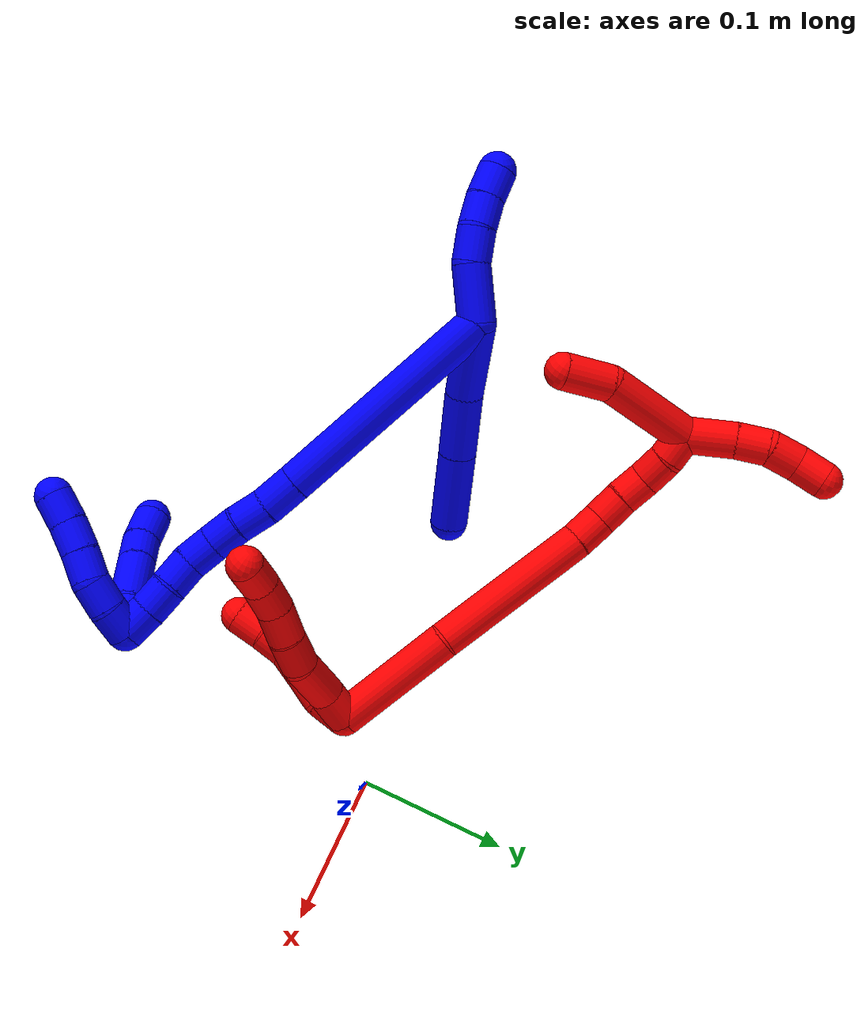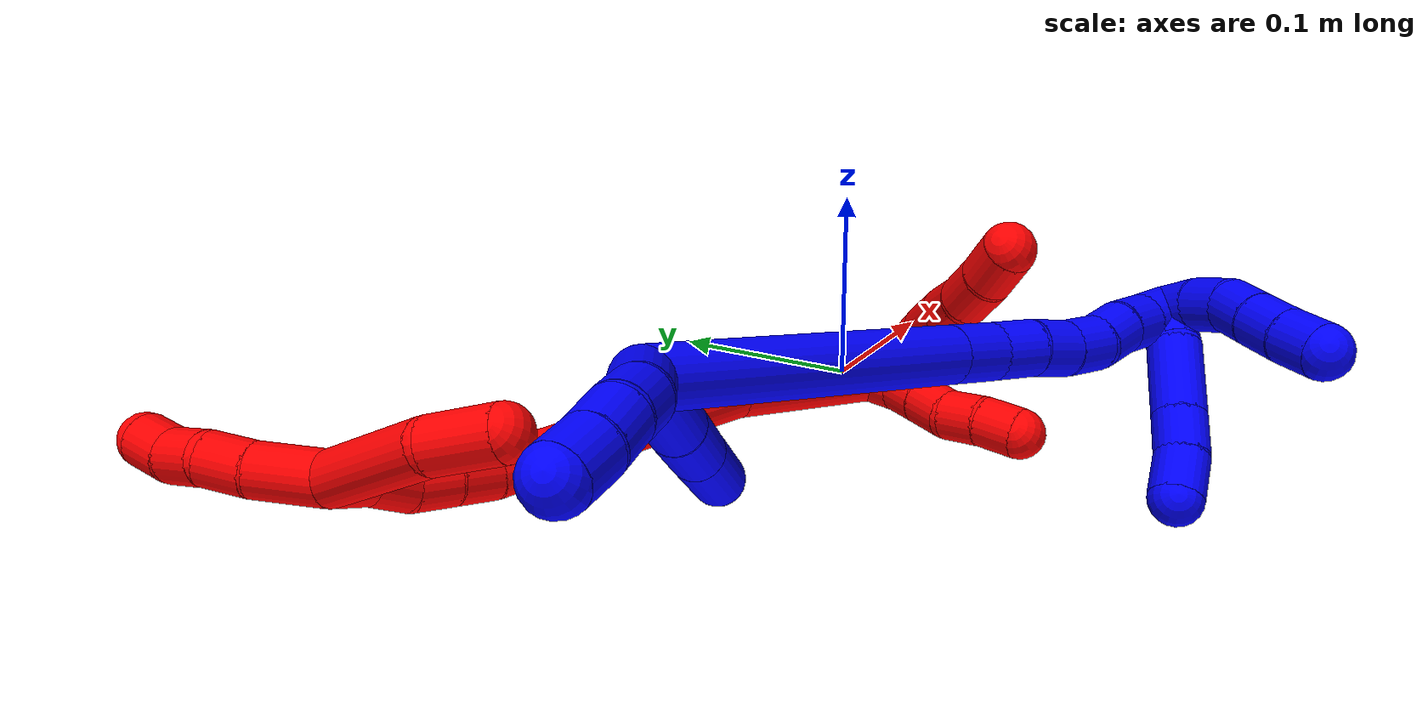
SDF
<sdf version="1.7">
 <world name="default">
  <plugin name="TubeGeneratorPlugin" filename="libtube_generator_plugin.so"/>
  <model name="photoneo_s_sensor">
   <static>1</static>
   <pose>0 0 2 1.57079 1.57079 3.14159</pose>
   <link name="link">
    <inertial><mass>0.1</mass></inertial>
    <sensor name="sensor" type="depth">
     <update_rate>30</update_rate>
     <camera>
      <horizontal_fov>1.22</horizontal_fov>
      <image><width>1920</width><height>1200</height><format>B8G8R8</format></image>
      <clip><near>0.1</near><far>4</far></clip>
      <depth_camera><output>points</output></depth_camera>
     </camera>
     <plugin name="camera_plugin" filename="libgazebo_ros_depth_camera.so">
      <baseline>0.2</baseline>
      <alwaysOn>1</alwaysOn>
      <updateRate>0.0</updateRate>
      <cameraName>camera_ir</cameraName>
      <imageTopicName>/camera/color/image_raw</imageTopicName>
      <cameraInfoTopicName>/camera/color/camera_info</cameraInfoTopicName>
      <depthImageTopicName>/camera/depth/image_raw</depthImageTopicName>
      <depthImageCameraInfoTopicName>/camera/depth/camera_info</depthImageCameraInfoTopicName>
      <pointCloudTopicName>/camera/depth/points</pointCloudTopicName>
      <frameName>fr_optical</frameName>
      <pointCloudCutoff>0.1</pointCloudCutoff>
      <pointCloudCutoffMax>2.0</pointCloudCutoffMax>
      <distortionK1>0</distortionK1>
      <distortionK2>0</distortionK2>
      <distortionK3>0</distortionK3>
      <distortionT1>0</distortionT1>
      <distortionT2>0</distortionT2>
      <CxPrime>0</CxPrime>
      <Cx>0</Cx>
      <Cy>0</Cy>
      <focalLength>0</focalLength>
      <hackBaseline>0</hackBaseline>
     </plugin>
    </sensor>
   </link>
  </model>
  <gravity>0 0 -9.8</gravity>
  <magnetic_field>6e-06 2.3e-05 -4.2e-05</magnetic_field>
  <atmosphere type="adiabatic"/>
  <physics name="default_physics" default="0" type="ode">
   <max_step_size>0.003</max_step_size>
   <real_time_factor>1</real_time_factor>
   <real_time_update_rate>1000</real_time_update_rate>
   <max_contacts>10000</max_contacts>
   <ode>
    <solver>
     <type>quick</type>
     <iters>100</iters>
     <sor>1.3</sor>
     <use_dynamic_moi_rescaling>0</use_dynamic_moi_rescaling>
    </solver>
    <constraints>
     <contact_max_correcting_vel>0</contact_max_correcting_vel>
     <contact_surface_layer>0.001</contact_surface_layer>
     <cfm>0</cfm>
     <erp>0.2</erp>
    </constraints>
   </ode>
  </physics>
  <scene><ambient>0.4 0.4 0.4 1</ambient><background>0.7 0.7 0.7 1</background><shadows>0</shadows></scene>
  <audio><device>default</device></audio>
  <spherical_coordinates>
   <surface_model>EARTH_WGS84</surface_model>
   <latitude_deg>0</latitude_deg>
   <longitude_deg>0</longitude_deg>
   <elevation>0</elevation>
   <heading_deg>0</heading_deg>
  </spherical_coordinates>
  <model name="bin">
   <static>1</static>
   <link name="bottom">
    <collision name="collision-bottom">
     <pose>0 0 -0.01 0 -0 0</pose>
     <geometry><box><size>0.8 0.6 0.02</size></box></geometry>
     <surface>
      <friction><ode><mu>100</mu><mu2>100</mu2></ode></friction>
      <contact><collide_bitmask>65535</collide_bitmask></contact>
     </surface>
    </collision>
   </link>
   <link name="west_wall">
    <collision name="collision-west_wall">
     <pose>-0.41 0 0.1 0 -0 0</pose>
     <geometry><box><size>0.02 0.6 0.2</size></box></geometry>
     <surface>
      <friction><ode><mu>100</mu><mu2>100</mu2></ode></friction>
      <contact><collide_bitmask>65535</collide_bitmask></contact>
     </surface>
    </collision>
   </link>
   <link name="east_wall">
    <collision name="collision-east_wall">
     <pose>0.41 0 0.1 0 -0 0</pose>
     <geometry><box><size>0.02 0.6 0.2</size></box></geometry>
     <surface>
      <friction><ode><mu>100</mu><mu2>100</mu2></ode></friction>
      <contact><collide_bitmask>65535</collide_bitmask></contact>
     </surface>
    </collision>
   </link>
   <link name="south_wall">
    <collision name="collision-south_wall">
     <pose>0 -0.31 0.1 0 -0 0</pose>
     <geometry><box><size>0.8 0.02 0.2</size></box></geometry>
     <surface>
      <friction><ode><mu>100</mu><mu2>100</mu2></ode></friction>
      <contact><collide_bitmask>65535</collide_bitmask></contact>
     </surface>
    </collision>
   </link>
   <link name="north_wall">
    <collision name="collision-north_wall">
     <pose>0 0.31 0.1 0 -0 0</pose>
     <geometry><box><size>0.8 0.02 0.2</size></box></geometry>
     <surface>
      <friction><ode><mu>100</mu><mu2>100</mu2></ode></friction>
      <contact><collide_bitmask>65535</collide_bitmask></contact>
     </surface>
    </collision>
   </link>
  </model>
  <model name="1">
   <static>0</static>
   <link name="1">
    <collision name="collision-cylinder-e_1_2_8">
     <pose>-0.002535 -0.001462 -0.025619 3.08459 -0.098456 -2.09243</pose>
     <geometry><cylinder><radius>0.0125</radius><length>0.051571</length></cylinder></geometry>
     <surface>
      <friction><ode><mu>1.16</mu><mu2>1.16</mu2><slip1>0</slip1><slip2>0</slip2></ode></friction>
      <contact><ode><kp>1e+06</kp><kd>1</kd><max_vel>0</max_vel><min_depth>0.001</min_depth></ode></contact>
     </surface>
    </collision>
    <visual name="visual-cylinder-e_1_2_8">
     <pose>-0.002535 -0.001462 -0.025619 3.08459 -0.098456 -2.09243</pose>
     <geometry><cylinder><radius>0.0125</radius><length>0.051571</length></cylinder></geometry>
     <material><ambient>0 0 1 1</ambient></material>
    </visual>
    <collision name="collision-cylinder-e_2_8_9">
     <pose>-0.005978 -0.002462 -0.073418 -3.12076 -0.040922 2.19975</pose>
     <geometry><cylinder><radius>0.0125</radius><length>0.044406</length></cylinder></geometry>
     <surface>
      <friction><ode><mu>1.16</mu><mu2>1.16</mu2><slip1>0</slip1><slip2>0</slip2></ode></friction>
      <contact><ode><kp>1e+06</kp><kd>1</kd><max_vel>0</max_vel><min_depth>0.001</min_depth></ode></contact>
     </surface>
    </collision>
    <visual name="visual-cylinder-e_2_8_9">
     <pose>-0.005978 -0.002462 -0.073418 -3.12076 -0.040922 2.19975</pose>
     <geometry><cylinder><radius>0.0125</radius><length>0.044406</length></cylinder></geometry>
     <material><ambient>0 0 1 1</ambient></material>
    </visual>
    <collision name="collision-cylinder-e_3_9_6">
     <pose>-0.00782 -0.001581 -0.122589 -3.1261 -0.034585 2.29958</pose>
     <geometry><cylinder><radius>0.0125</radius><length>0.054023</length></cylinder></geometry>
     <surface>
      <friction><ode><mu>1.16</mu><mu2>1.16</mu2><slip1>0</slip1><slip2>0</slip2></ode></friction>
      <contact><ode><kp>1e+06</kp><kd>1</kd><max_vel>0</max_vel><min_depth>0.001</min_depth></ode></contact>
     </surface>
    </collision>
    <visual name="visual-cylinder-e_3_9_6">
     <pose>-0.00782 -0.001581 -0.122589 -3.1261 -0.034585 2.29958</pose>
     <geometry><cylinder><radius>0.0125</radius><length>0.054023</length></cylinder></geometry>
     <material><ambient>0 0 1 1</ambient></material>
    </visual>
    <collision name="collision-cylinder-e_1_2_10">
     <pose>-0.005507 -0.006507 0.016806 0.369395 -0.296572 -0.055803</pose>
     <geometry><cylinder><radius>0.0125</radius><length>0.03769</length></cylinder></geometry>
     <surface>
      <friction><ode><mu>1.16</mu><mu2>1.16</mu2><slip1>0</slip1><slip2>0</slip2></ode></friction>
      <contact><ode><kp>1e+06</kp><kd>1</kd><max_vel>0</max_vel><min_depth>0.001</min_depth></ode></contact>
     </surface>
    </collision>
    <visual name="visual-cylinder-e_1_2_10">
     <pose>-0.005507 -0.006507 0.016806 0.369395 -0.296572 -0.055803</pose>
     <geometry><cylinder><radius>0.0125</radius><length>0.03769</length></cylinder></geometry>
     <material><ambient>0 0 1 1</ambient></material>
    </visual>
    <collision name="collision-cylinder-e_2_10_11">
     <pose>-0.016206 -0.014443 0.043252 0.147212 -0.489498 -0.036829</pose>
     <geometry><cylinder><radius>0.0125</radius><length>0.022081</length></cylinder></geometry>
     <surface>
      <friction><ode><mu>1.16</mu><mu2>1.16</mu2><slip1>0</slip1><slip2>0</slip2></ode></friction>
      <contact><ode><kp>1e+06</kp><kd>1</kd><max_vel>0</max_vel><min_depth>0.001</min_depth></ode></contact>
     </surface>
    </collision>
    <visual name="visual-cylinder-e_2_10_11">
     <pose>-0.016206 -0.014443 0.043252 0.147212 -0.489498 -0.036829</pose>
     <geometry><cylinder><radius>0.0125</radius><length>0.022081</length></cylinder></geometry>
     <material><ambient>0 0 1 1</ambient></material>
    </visual>
    <collision name="collision-cylinder-e_3_11_12">
     <pose>-0.027913 -0.01665 0.060553 0.101083 -0.702196 -0.037051</pose>
     <geometry><cylinder><radius>0.0125</radius><length>0.020177</length></cylinder></geometry>
     <surface>
      <friction><ode><mu>1.16</mu><mu2>1.16</mu2><slip1>0</slip1><slip2>0</slip2></ode></friction>
      <contact><ode><kp>1e+06</kp><kd>1</kd><max_vel>0</max_vel><min_depth>0.001</min_depth></ode></contact>
     </surface>
    </collision>
    <visual name="visual-cylinder-e_3_11_12">
     <pose>-0.027913 -0.01665 0.060553 0.101083 -0.702196 -0.037051</pose>
     <geometry><cylinder><radius>0.0125</radius><length>0.020177</length></cylinder></geometry>
     <material><ambient>0 0 1 1</ambient></material>
    </visual>
    <collision name="collision-cylinder-e_4_12_5">
     <pose>-0.041192 -0.016978 0.075604 -0.060632 -0.74032 0.023534</pose>
     <geometry><cylinder><radius>0.0125</radius><length>0.020052</length></cylinder></geometry>
     <surface>
      <friction><ode><mu>1.16</mu><mu2>1.16</mu2><slip1>0</slip1><slip2>0</slip2></ode></friction>
      <contact><ode><kp>1e+06</kp><kd>1</kd><max_vel>0</max_vel><min_depth>0.001</min_depth></ode></contact>
     </surface>
    </collision>
    <visual name="visual-cylinder-e_4_12_5">
     <pose>-0.041192 -0.016978 0.075604 -0.060632 -0.74032 0.023534</pose>
     <geometry><cylinder><radius>0.0125</radius><length>0.020052</length></cylinder></geometry>
     <material><ambient>0 0 1 1</ambient></material>
    </visual>
    <collision name="collision-cylinder-e_1_2_13">
     <pose>0.03582 -0.041221 -0.053983 2.48944 0.485305 1.26379</pose>
     <geometry><cylinder><radius>0.0125</radius><length>0.153576</length></cylinder></geometry>
     <surface>
      <friction><ode><mu>1.16</mu><mu2>1.16</mu2><slip1>0</slip1><slip2>0</slip2></ode></friction>
      <contact><ode><kp>1e+06</kp><kd>1</kd><max_vel>0</max_vel><min_depth>0.001</min_depth></ode></contact>
     </surface>
    </collision>
    <visual name="visual-cylinder-e_1_2_13">
     <pose>0.03582 -0.041221 -0.053983 2.48944 0.485305 1.26379</pose>
     <geometry><cylinder><radius>0.0125</radius><length>0.153576</length></cylinder></geometry>
     <material><ambient>0 0 1 1</ambient></material>
    </visual>
    <collision name="collision-cylinder-e_2_13_14">
     <pose>0.077329 -0.089137 -0.116417 2.47172 0.48551 1.23681</pose>
     <geometry><cylinder><radius>0.0125</radius><length>0.024381</length></cylinder></geometry>
     <surface>
      <friction><ode><mu>1.16</mu><mu2>1.16</mu2><slip1>0</slip1><slip2>0</slip2></ode></friction>
      <contact><ode><kp>1e+06</kp><kd>1</kd><max_vel>0</max_vel><min_depth>0.001</min_depth></ode></contact>
     </surface>
    </collision>
    <visual name="visual-cylinder-e_2_13_14">
     <pose>0.077329 -0.089137 -0.116417 2.47172 0.48551 1.23681</pose>
     <geometry><cylinder><radius>0.0125</radius><length>0.024381</length></cylinder></geometry>
     <material><ambient>0 0 1 1</ambient></material>
    </visual>
    <collision name="collision-cylinder-e_3_14_15">
     <pose>0.088333 -0.102736 -0.131226 2.31498 0.515341 1.08213</pose>
     <geometry><cylinder><radius>0.0125</radius><length>0.021572</length></cylinder></geometry>
     <surface>
      <friction><ode><mu>1.16</mu><mu2>1.16</mu2><slip1>0</slip1><slip2>0</slip2></ode></friction>
      <contact><ode><kp>1e+06</kp><kd>1</kd><max_vel>0</max_vel><min_depth>0.001</min_depth></ode></contact>
     </surface>
    </collision>
    <visual name="visual-cylinder-e_3_14_15">
     <pose>0.088333 -0.102736 -0.131226 2.31498 0.515341 1.08213</pose>
     <geometry><cylinder><radius>0.0125</radius><length>0.021572</length></cylinder></geometry>
     <material><ambient>0 0 1 1</ambient></material>
    </visual>
    <collision name="collision-cylinder-e_4_15_16">
     <pose>0.097808 -0.115694 -0.144506 2.42303 0.424709 1.04225</pose>
     <geometry><cylinder><radius>0.0125</radius><length>0.020188</length></cylinder></geometry>
     <surface>
      <friction><ode><mu>1.16</mu><mu2>1.16</mu2><slip1>0</slip1><slip2>0</slip2></ode></friction>
      <contact><ode><kp>1e+06</kp><kd>1</kd><max_vel>0</max_vel><min_depth>0.001</min_depth></ode></contact>
     </surface>
    </collision>
    <visual name="visual-cylinder-e_4_15_16">
     <pose>0.097808 -0.115694 -0.144506 2.42303 0.424709 1.04225</pose>
     <geometry><cylinder><radius>0.0125</radius><length>0.020188</length></cylinder></geometry>
     <material><ambient>0 0 1 1</ambient></material>
    </visual>
    <collision name="collision-cylinder-e_5_16_17">
     <pose>0.107381 -0.127225 -0.157873 2.43717 0.569427 1.34494</pose>
     <geometry><cylinder><radius>0.0125</radius><length>0.02008</length></cylinder></geometry>
     <surface>
      <friction><ode><mu>1.16</mu><mu2>1.16</mu2><slip1>0</slip1><slip2>0</slip2></ode></friction>
      <contact><ode><kp>1e+06</kp><kd>1</kd><max_vel>0</max_vel><min_depth>0.001</min_depth></ode></contact>
     </surface>
    </collision>
    <visual name="visual-cylinder-e_5_16_17">
     <pose>0.107381 -0.127225 -0.157873 2.43717 0.569427 1.34494</pose>
     <geometry><cylinder><radius>0.0125</radius><length>0.02008</length></cylinder></geometry>
     <material><ambient>0 0 1 1</ambient></material>
    </visual>
    <collision name="collision-cylinder-e_6_17_18">
     <pose>0.119664 -0.135929 -0.170852 2.68289 0.755819 2.07838</pose>
     <geometry><cylinder><radius>0.0125</radius><length>0.020035</length></cylinder></geometry>
     <surface>
      <friction><ode><mu>1.16</mu><mu2>1.16</mu2><slip1>0</slip1><slip2>0</slip2></ode></friction>
      <contact><ode><kp>1e+06</kp><kd>1</kd><max_vel>0</max_vel><min_depth>0.001</min_depth></ode></contact>
     </surface>
    </collision>
    <visual name="visual-cylinder-e_6_17_18">
     <pose>0.119664 -0.135929 -0.170852 2.68289 0.755819 2.07838</pose>
     <geometry><cylinder><radius>0.0125</radius><length>0.020035</length></cylinder></geometry>
     <material><ambient>0 0 1 1</ambient></material>
    </visual>
    <collision name="collision-cylinder-e_7_18_19">
     <pose>0.132104 -0.143107 -0.184719 2.64729 0.589438 1.75468</pose>
     <geometry><cylinder><radius>0.0125</radius><length>0.020037</length></cylinder></geometry>
     <surface>
      <friction><ode><mu>1.16</mu><mu2>1.16</mu2><slip1>0</slip1><slip2>0</slip2></ode></friction>
      <contact><ode><kp>1e+06</kp><kd>1</kd><max_vel>0</max_vel><min_depth>0.001</min_depth></ode></contact>
     </surface>
    </collision>
    <visual name="visual-cylinder-e_7_18_19">
     <pose>0.132104 -0.143107 -0.184719 2.64729 0.589438 1.75468</pose>
     <geometry><cylinder><radius>0.0125</radius><length>0.020037</length></cylinder></geometry>
     <material><ambient>0 0 1 1</ambient></material>
    </visual>
    <collision name="collision-cylinder-e_8_19_1">
     <pose>0.143742 -0.151553 -0.198706 2.54765 0.647048 1.66206</pose>
     <geometry><cylinder><radius>0.0125</radius><length>0.020131</length></cylinder></geometry>
     <surface>
      <friction><ode><mu>1.16</mu><mu2>1.16</mu2><slip1>0</slip1><slip2>0</slip2></ode></friction>
      <contact><ode><kp>1e+06</kp><kd>1</kd><max_vel>0</max_vel><min_depth>0.001</min_depth></ode></contact>
     </surface>
    </collision>
    <visual name="visual-cylinder-e_8_19_1">
     <pose>0.143742 -0.151553 -0.198706 2.54765 0.647048 1.66206</pose>
     <geometry><cylinder><radius>0.0125</radius><length>0.020131</length></cylinder></geometry>
     <material><ambient>0 0 1 1</ambient></material>
    </visual>
    <collision name="collision-cylinder-e_1_1_20">
     <pose>0.141241 -0.160407 -0.200974 0.782208 -0.94545 -0.415657</pose>
     <geometry><cylinder><radius>0.0125</radius><length>0.021136</length></cylinder></geometry>
     <surface>
      <friction><ode><mu>1.16</mu><mu2>1.16</mu2><slip1>0</slip1><slip2>0</slip2></ode></friction>
      <contact><ode><kp>1e+06</kp><kd>1</kd><max_vel>0</max_vel><min_depth>0.001</min_depth></ode></contact>
     </surface>
    </collision>
    <visual name="visual-cylinder-e_1_1_20">
     <pose>0.141241 -0.160407 -0.200974 0.782208 -0.94545 -0.415657</pose>
     <geometry><cylinder><radius>0.0125</radius><length>0.021136</length></cylinder></geometry>
     <material><ambient>0 0 1 1</ambient></material>
    </visual>
    <collision name="collision-cylinder-e_2_20_21">
     <pose>0.116006 -0.171173 -0.191739 0.923075 -1.12173 -0.605628</pose>
     <geometry><cylinder><radius>0.0125</radius><length>0.037003</length></cylinder></geometry>
     <surface>
      <friction><ode><mu>1.16</mu><mu2>1.16</mu2><slip1>0</slip1><slip2>0</slip2></ode></friction>
      <contact><ode><kp>1e+06</kp><kd>1</kd><max_vel>0</max_vel><min_depth>0.001</min_depth></ode></contact>
     </surface>
    </collision>
    <visual name="visual-cylinder-e_2_20_21">
     <pose>0.116006 -0.171173 -0.191739 0.923075 -1.12173 -0.605628</pose>
     <geometry><cylinder><radius>0.0125</radius><length>0.037003</length></cylinder></geometry>
     <material><ambient>0 0 1 1</ambient></material>
    </visual>
    <collision name="collision-cylinder-e_3_21_22">
     <pose>0.090287 -0.181013 -0.184216 0.908837 -1.12238 -0.595891</pose>
     <geometry><cylinder><radius>0.0125</radius><length>0.020091</length></cylinder></geometry>
     <surface>
      <friction><ode><mu>1.16</mu><mu2>1.16</mu2><slip1>0</slip1><slip2>0</slip2></ode></friction>
      <contact><ode><kp>1e+06</kp><kd>1</kd><max_vel>0</max_vel><min_depth>0.001</min_depth></ode></contact>
     </surface>
    </collision>
    <visual name="visual-cylinder-e_3_21_22">
     <pose>0.090287 -0.181013 -0.184216 0.908837 -1.12238 -0.595891</pose>
     <geometry><cylinder><radius>0.0125</radius><length>0.020091</length></cylinder></geometry>
     <material><ambient>0 0 1 1</ambient></material>
    </visual>
    <collision name="collision-cylinder-e_4_22_4">
     <pose>0.071094 -0.186182 -0.177982 0.453423 -1.1988 -0.312653</pose>
     <geometry><cylinder><radius>0.0125</radius><length>0.02177</length></cylinder></geometry>
     <surface>
      <friction><ode><mu>1.16</mu><mu2>1.16</mu2><slip1>0</slip1><slip2>0</slip2></ode></friction>
      <contact><ode><kp>1e+06</kp><kd>1</kd><max_vel>0</max_vel><min_depth>0.001</min_depth></ode></contact>
     </surface>
    </collision>
    <visual name="visual-cylinder-e_4_22_4">
     <pose>0.071094 -0.186182 -0.177982 0.453423 -1.1988 -0.312653</pose>
     <geometry><cylinder><radius>0.0125</radius><length>0.02177</length></cylinder></geometry>
     <material><ambient>0 0 1 1</ambient></material>
    </visual>
    <collision name="collision-cylinder-e_1_1_23">
     <pose>0.151468 -0.162137 -0.197606 0.665676 0.166664 0.057733</pose>
     <geometry><cylinder><radius>0.0125</radius><length>0.02</length></cylinder></geometry>
     <surface>
      <friction><ode><mu>1.16</mu><mu2>1.16</mu2><slip1>0</slip1><slip2>0</slip2></ode></friction>
      <contact><ode><kp>1e+06</kp><kd>1</kd><max_vel>0</max_vel><min_depth>0.001</min_depth></ode></contact>
     </surface>
    </collision>
    <visual name="visual-cylinder-e_1_1_23">
     <pose>0.151468 -0.162137 -0.197606 0.665676 0.166664 0.057733</pose>
     <geometry><cylinder><radius>0.0125</radius><length>0.02</length></cylinder></geometry>
     <material><ambient>0 0 1 1</ambient></material>
    </visual>
    <collision name="collision-cylinder-e_2_23_24">
     <pose>0.152808 -0.174753 -0.182279 0.71137 -0.031967 -0.011876</pose>
     <geometry><cylinder><radius>0.0125</radius><length>0.02</length></cylinder></geometry>
     <surface>
      <friction><ode><mu>1.16</mu><mu2>1.16</mu2><slip1>0</slip1><slip2>0</slip2></ode></friction>
      <contact><ode><kp>1e+06</kp><kd>1</kd><max_vel>0</max_vel><min_depth>0.001</min_depth></ode></contact>
     </surface>
    </collision>
    <visual name="visual-cylinder-e_2_23_24">
     <pose>0.152808 -0.174753 -0.182279 0.71137 -0.031967 -0.011876</pose>
     <geometry><cylinder><radius>0.0125</radius><length>0.02</length></cylinder></geometry>
     <material><ambient>0 0 1 1</ambient></material>
    </visual>
    <collision name="collision-cylinder-e_3_24_25">
     <pose>0.148919 -0.187371 -0.167627 0.710546 -0.364972 -0.13672</pose>
     <geometry><cylinder><radius>0.0125</radius><length>0.02</length></cylinder></geometry>
     <surface>
      <friction><ode><mu>1.16</mu><mu2>1.16</mu2><slip1>0</slip1><slip2>0</slip2></ode></friction>
      <contact><ode><kp>1e+06</kp><kd>1</kd><max_vel>0</max_vel><min_depth>0.001</min_depth></ode></contact>
     </surface>
    </collision>
    <visual name="visual-cylinder-e_3_24_25">
     <pose>0.148919 -0.187371 -0.167627 0.710546 -0.364972 -0.13672</pose>
     <geometry><cylinder><radius>0.0125</radius><length>0.02</length></cylinder></geometry>
     <material><ambient>0 0 1 1</ambient></material>
    </visual>
    <collision name="collision-cylinder-e_4_25_26">
     <pose>0.141959 -0.200131 -0.153909 0.78757 -0.345913 -0.144918</pose>
     <geometry><cylinder><radius>0.0125</radius><length>0.02</length></cylinder></geometry>
     <surface>
      <friction><ode><mu>1.16</mu><mu2>1.16</mu2><slip1>0</slip1><slip2>0</slip2></ode></friction>
      <contact><ode><kp>1e+06</kp><kd>1</kd><max_vel>0</max_vel><min_depth>0.001</min_depth></ode></contact>
     </surface>
    </collision>
    <visual name="visual-cylinder-e_4_25_26">
     <pose>0.141959 -0.200131 -0.153909 0.78757 -0.345913 -0.144918</pose>
     <geometry><cylinder><radius>0.0125</radius><length>0.02</length></cylinder></geometry>
     <material><ambient>0 0 1 1</ambient></material>
    </visual>
    <collision name="collision-cylinder-e_5_26_3">
     <pose>0.135774 -0.213955 -0.140872 0.841283 -0.283246 -0.127389</pose>
     <geometry><cylinder><radius>0.0125</radius><length>0.02</length></cylinder></geometry>
     <surface>
      <friction><ode><mu>1.16</mu><mu2>1.16</mu2><slip1>0</slip1><slip2>0</slip2></ode></friction>
      <contact><ode><kp>1e+06</kp><kd>1</kd><max_vel>0</max_vel><min_depth>0.001</min_depth></ode></contact>
     </surface>
    </collision>
    <visual name="visual-cylinder-e_5_26_3">
     <pose>0.135774 -0.213955 -0.140872 0.841283 -0.283246 -0.127389</pose>
     <geometry><cylinder><radius>0.0125</radius><length>0.02</length></cylinder></geometry>
     <material><ambient>0 0 1 1</ambient></material>
    </visual>
    <collision name="collision-sphere-3">
     <pose>0.132979 -0.221113 -0.134472 0 -0 0</pose>
     <geometry><sphere><radius>0.0125</radius></sphere></geometry>
     <surface>
      <friction><ode><mu>1.16</mu><mu2>1.16</mu2><slip1>0</slip1><slip2>0</slip2></ode></friction>
      <contact><ode><kp>1e+06</kp><kd>1</kd><max_vel>0</max_vel><min_depth>0.001</min_depth></ode></contact>
     </surface>
    </collision>
    <visual name="visual-sphere-3">
     <pose>0.132979 -0.221113 -0.134472 0 -0 0</pose>
     <geometry><sphere><radius>0.0125</radius></sphere></geometry>
     <material><ambient>0 0 1 1</ambient></material>
    </visual>
    <collision name="collision-sphere-26">
     <pose>0.138568 -0.206797 -0.147271 0 -0 0</pose>
     <geometry><sphere><radius>0.0125</radius></sphere></geometry>
     <surface>
      <friction><ode><mu>1.16</mu><mu2>1.16</mu2><slip1>0</slip1><slip2>0</slip2></ode></friction>
      <contact><ode><kp>1e+06</kp><kd>1</kd><max_vel>0</max_vel><min_depth>0.001</min_depth></ode></contact>
     </surface>
    </collision>
    <visual name="visual-sphere-26">
     <pose>0.138568 -0.206797 -0.147271 0 -0 0</pose>
     <geometry><sphere><radius>0.0125</radius></sphere></geometry>
     <material><ambient>0 0 1 1</ambient></material>
    </visual>
    <collision name="collision-sphere-25">
     <pose>0.145349 -0.193464 -0.160547 0 -0 0</pose>
     <geometry><sphere><radius>0.0125</radius></sphere></geometry>
     <surface>
      <friction><ode><mu>1.16</mu><mu2>1.16</mu2><slip1>0</slip1><slip2>0</slip2></ode></friction>
      <contact><ode><kp>1e+06</kp><kd>1</kd><max_vel>0</max_vel><min_depth>0.001</min_depth></ode></contact>
     </surface>
    </collision>
    <visual name="visual-sphere-25">
     <pose>0.145349 -0.193464 -0.160547 0 -0 0</pose>
     <geometry><sphere><radius>0.0125</radius></sphere></geometry>
     <material><ambient>0 0 1 1</ambient></material>
    </visual>
    <collision name="collision-sphere-24">
     <pose>0.152488 -0.181278 -0.174708 0 -0 0</pose>
     <geometry><sphere><radius>0.0125</radius></sphere></geometry>
     <surface>
      <friction><ode><mu>1.16</mu><mu2>1.16</mu2><slip1>0</slip1><slip2>0</slip2></ode></friction>
      <contact><ode><kp>1e+06</kp><kd>1</kd><max_vel>0</max_vel><min_depth>0.001</min_depth></ode></contact>
     </surface>
    </collision>
    <visual name="visual-sphere-24">
     <pose>0.152488 -0.181278 -0.174708 0 -0 0</pose>
     <geometry><sphere><radius>0.0125</radius></sphere></geometry>
     <material><ambient>0 0 1 1</ambient></material>
    </visual>
    <collision name="collision-sphere-23">
     <pose>0.153127 -0.168228 -0.18985 0 -0 0</pose>
     <geometry><sphere><radius>0.0125</radius></sphere></geometry>
     <surface>
      <friction><ode><mu>1.16</mu><mu2>1.16</mu2><slip1>0</slip1><slip2>0</slip2></ode></friction>
      <contact><ode><kp>1e+06</kp><kd>1</kd><max_vel>0</max_vel><min_depth>0.001</min_depth></ode></contact>
     </surface>
    </collision>
    <visual name="visual-sphere-23">
     <pose>0.153127 -0.168228 -0.18985 0 -0 0</pose>
     <geometry><sphere><radius>0.0125</radius></sphere></geometry>
     <material><ambient>0 0 1 1</ambient></material>
    </visual>
    <collision name="collision-sphere-4">
     <pose>0.060953 -0.187915 -0.174426 0 -0 0</pose>
     <geometry><sphere><radius>0.0125</radius></sphere></geometry>
     <surface>
      <friction><ode><mu>1.16</mu><mu2>1.16</mu2><slip1>0</slip1><slip2>0</slip2></ode></friction>
      <contact><ode><kp>1e+06</kp><kd>1</kd><max_vel>0</max_vel><min_depth>0.001</min_depth></ode></contact>
     </surface>
    </collision>
    <visual name="visual-sphere-4">
     <pose>0.060953 -0.187915 -0.174426 0 -0 0</pose>
     <geometry><sphere><radius>0.0125</radius></sphere></geometry>
     <material><ambient>0 0 1 1</ambient></material>
    </visual>
    <collision name="collision-sphere-22">
     <pose>0.081234 -0.184449 -0.181539 0 -0 0</pose>
     <geometry><sphere><radius>0.0125</radius></sphere></geometry>
     <surface>
      <friction><ode><mu>1.16</mu><mu2>1.16</mu2><slip1>0</slip1><slip2>0</slip2></ode></friction>
      <contact><ode><kp>1e+06</kp><kd>1</kd><max_vel>0</max_vel><min_depth>0.001</min_depth></ode></contact>
     </surface>
    </collision>
    <visual name="visual-sphere-22">
     <pose>0.081234 -0.184449 -0.181539 0 -0 0</pose>
     <geometry><sphere><radius>0.0125</radius></sphere></geometry>
     <material><ambient>0 0 1 1</ambient></material>
    </visual>
    <collision name="collision-sphere-21">
     <pose>0.099339 -0.177578 -0.186893 0 -0 0</pose>
     <geometry><sphere><radius>0.0125</radius></sphere></geometry>
     <surface>
      <friction><ode><mu>1.16</mu><mu2>1.16</mu2><slip1>0</slip1><slip2>0</slip2></ode></friction>
      <contact><ode><kp>1e+06</kp><kd>1</kd><max_vel>0</max_vel><min_depth>0.001</min_depth></ode></contact>
     </surface>
    </collision>
    <visual name="visual-sphere-21">
     <pose>0.099339 -0.177578 -0.186893 0 -0 0</pose>
     <geometry><sphere><radius>0.0125</radius></sphere></geometry>
     <material><ambient>0 0 1 1</ambient></material>
    </visual>
    <collision name="collision-sphere-20">
     <pose>0.132673 -0.164768 -0.196585 0 -0 0</pose>
     <geometry><sphere><radius>0.0125</radius></sphere></geometry>
     <surface>
      <friction><ode><mu>1.16</mu><mu2>1.16</mu2><slip1>0</slip1><slip2>0</slip2></ode></friction>
      <contact><ode><kp>1e+06</kp><kd>1</kd><max_vel>0</max_vel><min_depth>0.001</min_depth></ode></contact>
     </surface>
    </collision>
    <visual name="visual-sphere-20">
     <pose>0.132673 -0.164768 -0.196585 0 -0 0</pose>
     <geometry><sphere><radius>0.0125</radius></sphere></geometry>
     <material><ambient>0 0 1 1</ambient></material>
    </visual>
    <collision name="collision-sphere-11">
     <pose>-0.021397 -0.015872 0.05289 0 -0 0</pose>
     <geometry><sphere><radius>0.0125</radius></sphere></geometry>
     <surface>
      <friction><ode><mu>1.16</mu><mu2>1.16</mu2><slip1>0</slip1><slip2>0</slip2></ode></friction>
      <contact><ode><kp>1e+06</kp><kd>1</kd><max_vel>0</max_vel><min_depth>0.001</min_depth></ode></contact>
     </surface>
    </collision>
    <visual name="visual-sphere-11">
     <pose>-0.021397 -0.015872 0.05289 0 -0 0</pose>
     <geometry><sphere><radius>0.0125</radius></sphere></geometry>
     <material><ambient>0 0 1 1</ambient></material>
    </visual>
    <collision name="collision-sphere-10">
     <pose>-0.011015 -0.013014 0.033613 0 -0 0</pose>
     <geometry><sphere><radius>0.0125</radius></sphere></geometry>
     <surface>
      <friction><ode><mu>1.16</mu><mu2>1.16</mu2><slip1>0</slip1><slip2>0</slip2></ode></friction>
      <contact><ode><kp>1e+06</kp><kd>1</kd><max_vel>0</max_vel><min_depth>0.001</min_depth></ode></contact>
     </surface>
    </collision>
    <visual name="visual-sphere-10">
     <pose>-0.011015 -0.013014 0.033613 0 -0 0</pose>
     <geometry><sphere><radius>0.0125</radius></sphere></geometry>
     <material><ambient>0 0 1 1</ambient></material>
    </visual>
    <collision name="collision-sphere-6">
     <pose>-0.008754 -0.001163 -0.149581 0 -0 0</pose>
     <geometry><sphere><radius>0.0125</radius></sphere></geometry>
     <surface>
      <friction><ode><mu>1.16</mu><mu2>1.16</mu2><slip1>0</slip1><slip2>0</slip2></ode></friction>
      <contact><ode><kp>1e+06</kp><kd>1</kd><max_vel>0</max_vel><min_depth>0.001</min_depth></ode></contact>
     </surface>
    </collision>
    <visual name="visual-sphere-6">
     <pose>-0.008754 -0.001163 -0.149581 0 -0 0</pose>
     <geometry><sphere><radius>0.0125</radius></sphere></geometry>
     <material><ambient>0 0 1 1</ambient></material>
    </visual>
    <collision name="collision-sphere-9">
     <pose>-0.006886 -0.001999 -0.095597 0 -0 0</pose>
     <geometry><sphere><radius>0.0125</radius></sphere></geometry>
     <surface>
      <friction><ode><mu>1.16</mu><mu2>1.16</mu2><slip1>0</slip1><slip2>0</slip2></ode></friction>
      <contact><ode><kp>1e+06</kp><kd>1</kd><max_vel>0</max_vel><min_depth>0.001</min_depth></ode></contact>
     </surface>
    </collision>
    <visual name="visual-sphere-9">
     <pose>-0.006886 -0.001999 -0.095597 0 -0 0</pose>
     <geometry><sphere><radius>0.0125</radius></sphere></geometry>
     <material><ambient>0 0 1 1</ambient></material>
    </visual>
    <collision name="collision-sphere-2">
     <geometry><sphere><radius>0.0125</radius></sphere></geometry>
     <surface>
      <friction><ode><mu>1.16</mu><mu2>1.16</mu2><slip1>0</slip1><slip2>0</slip2></ode></friction>
      <contact><ode><kp>1e+06</kp><kd>1</kd><max_vel>0</max_vel><min_depth>0.001</min_depth></ode></contact>
     </surface>
    </collision>
    <visual name="visual-sphere-2">
     <geometry><sphere><radius>0.0125</radius></sphere></geometry>
     <material><ambient>0 0 1 1</ambient></material>
    </visual>
    <collision name="collision-sphere-19">
     <pose>0.137674 -0.147058 -0.192051 0 -0 0</pose>
     <geometry><sphere><radius>0.0125</radius></sphere></geometry>
     <surface>
      <friction><ode><mu>1.16</mu><mu2>1.16</mu2><slip1>0</slip1><slip2>0</slip2></ode></friction>
      <contact><ode><kp>1e+06</kp><kd>1</kd><max_vel>0</max_vel><min_depth>0.001</min_depth></ode></contact>
     </surface>
    </collision>
    <visual name="visual-sphere-19">
     <pose>0.137674 -0.147058 -0.192051 0 -0 0</pose>
     <geometry><sphere><radius>0.0125</radius></sphere></geometry>
     <material><ambient>0 0 1 1</ambient></material>
    </visual>
    <collision name="collision-sphere-8">
     <pose>-0.005069 -0.002924 -0.051238 0 -0 0</pose>
     <geometry><sphere><radius>0.0125</radius></sphere></geometry>
     <surface>
      <friction><ode><mu>1.16</mu><mu2>1.16</mu2><slip1>0</slip1><slip2>0</slip2></ode></friction>
      <contact><ode><kp>1e+06</kp><kd>1</kd><max_vel>0</max_vel><min_depth>0.001</min_depth></ode></contact>
     </surface>
    </collision>
    <visual name="visual-sphere-8">
     <pose>-0.005069 -0.002924 -0.051238 0 -0 0</pose>
     <geometry><sphere><radius>0.0125</radius></sphere></geometry>
     <material><ambient>0 0 1 1</ambient></material>
    </visual>
    <collision name="collision-sphere-12">
     <pose>-0.034429 -0.017427 0.068216 0 -0 0</pose>
     <geometry><sphere><radius>0.0125</radius></sphere></geometry>
     <surface>
      <friction><ode><mu>1.16</mu><mu2>1.16</mu2><slip1>0</slip1><slip2>0</slip2></ode></friction>
      <contact><ode><kp>1e+06</kp><kd>1</kd><max_vel>0</max_vel><min_depth>0.001</min_depth></ode></contact>
     </surface>
    </collision>
    <visual name="visual-sphere-12">
     <pose>-0.034429 -0.017427 0.068216 0 -0 0</pose>
     <geometry><sphere><radius>0.0125</radius></sphere></geometry>
     <material><ambient>0 0 1 1</ambient></material>
    </visual>
    <collision name="collision-sphere-5">
     <pose>-0.047955 -0.01653 0.082992 0 -0 0</pose>
     <geometry><sphere><radius>0.0125</radius></sphere></geometry>
     <surface>
      <friction><ode><mu>1.16</mu><mu2>1.16</mu2><slip1>0</slip1><slip2>0</slip2></ode></friction>
      <contact><ode><kp>1e+06</kp><kd>1</kd><max_vel>0</max_vel><min_depth>0.001</min_depth></ode></contact>
     </surface>
    </collision>
    <visual name="visual-sphere-5">
     <pose>-0.047955 -0.01653 0.082992 0 -0 0</pose>
     <geometry><sphere><radius>0.0125</radius></sphere></geometry>
     <material><ambient>0 0 1 1</ambient></material>
    </visual>
    <collision name="collision-sphere-13">
     <pose>0.07164 -0.082443 -0.107965 0 -0 0</pose>
     <geometry><sphere><radius>0.0125</radius></sphere></geometry>
     <surface>
      <friction><ode><mu>1.16</mu><mu2>1.16</mu2><slip1>0</slip1><slip2>0</slip2></ode></friction>
      <contact><ode><kp>1e+06</kp><kd>1</kd><max_vel>0</max_vel><min_depth>0.001</min_depth></ode></contact>
     </surface>
    </collision>
    <visual name="visual-sphere-13">
     <pose>0.07164 -0.082443 -0.107965 0 -0 0</pose>
     <geometry><sphere><radius>0.0125</radius></sphere></geometry>
     <material><ambient>0 0 1 1</ambient></material>
    </visual>
    <collision name="collision-sphere-14">
     <pose>0.083018 -0.095832 -0.124869 0 -0 0</pose>
     <geometry><sphere><radius>0.0125</radius></sphere></geometry>
     <surface>
      <friction><ode><mu>1.16</mu><mu2>1.16</mu2><slip1>0</slip1><slip2>0</slip2></ode></friction>
      <contact><ode><kp>1e+06</kp><kd>1</kd><max_vel>0</max_vel><min_depth>0.001</min_depth></ode></contact>
     </surface>
    </collision>
    <visual name="visual-sphere-14">
     <pose>0.083018 -0.095832 -0.124869 0 -0 0</pose>
     <geometry><sphere><radius>0.0125</radius></sphere></geometry>
     <material><ambient>0 0 1 1</ambient></material>
    </visual>
    <collision name="collision-sphere-15">
     <pose>0.093649 -0.10964 -0.137583 0 -0 0</pose>
     <geometry><sphere><radius>0.0125</radius></sphere></geometry>
     <surface>
      <friction><ode><mu>1.16</mu><mu2>1.16</mu2><slip1>0</slip1><slip2>0</slip2></ode></friction>
      <contact><ode><kp>1e+06</kp><kd>1</kd><max_vel>0</max_vel><min_depth>0.001</min_depth></ode></contact>
     </surface>
    </collision>
    <visual name="visual-sphere-15">
     <pose>0.093649 -0.10964 -0.137583 0 -0 0</pose>
     <geometry><sphere><radius>0.0125</radius></sphere></geometry>
     <material><ambient>0 0 1 1</ambient></material>
    </visual>
    <collision name="collision-sphere-16">
     <pose>0.101967 -0.121749 -0.15143 0 -0 0</pose>
     <geometry><sphere><radius>0.0125</radius></sphere></geometry>
     <surface>
      <friction><ode><mu>1.16</mu><mu2>1.16</mu2><slip1>0</slip1><slip2>0</slip2></ode></friction>
      <contact><ode><kp>1e+06</kp><kd>1</kd><max_vel>0</max_vel><min_depth>0.001</min_depth></ode></contact>
     </surface>
    </collision>
    <visual name="visual-sphere-16">
     <pose>0.101967 -0.121749 -0.15143 0 -0 0</pose>
     <geometry><sphere><radius>0.0125</radius></sphere></geometry>
     <material><ambient>0 0 1 1</ambient></material>
    </visual>
    <collision name="collision-sphere-17">
     <pose>0.112794 -0.132701 -0.164316 0 -0 0</pose>
     <geometry><sphere><radius>0.0125</radius></sphere></geometry>
     <surface>
      <friction><ode><mu>1.16</mu><mu2>1.16</mu2><slip1>0</slip1><slip2>0</slip2></ode></friction>
      <contact><ode><kp>1e+06</kp><kd>1</kd><max_vel>0</max_vel><min_depth>0.001</min_depth></ode></contact>
     </surface>
    </collision>
    <visual name="visual-sphere-17">
     <pose>0.112794 -0.132701 -0.164316 0 -0 0</pose>
     <geometry><sphere><radius>0.0125</radius></sphere></geometry>
     <material><ambient>0 0 1 1</ambient></material>
    </visual>
    <collision name="collision-sphere-18">
     <pose>0.126535 -0.139156 -0.177388 0 -0 0</pose>
     <geometry><sphere><radius>0.0125</radius></sphere></geometry>
     <surface>
      <friction><ode><mu>1.16</mu><mu2>1.16</mu2><slip1>0</slip1><slip2>0</slip2></ode></friction>
      <contact><ode><kp>1e+06</kp><kd>1</kd><max_vel>0</max_vel><min_depth>0.001</min_depth></ode></contact>
     </surface>
    </collision>
    <visual name="visual-sphere-18">
     <pose>0.126535 -0.139156 -0.177388 0 -0 0</pose>
     <geometry><sphere><radius>0.0125</radius></sphere></geometry>
     <material><ambient>0 0 1 1</ambient></material>
    </visual>
    <collision name="collision-sphere-1">
     <pose>0.149809 -0.156047 -0.205362 0 -0 0</pose>
     <geometry><sphere><radius>0.0125</radius></sphere></geometry>
     <surface>
      <friction><ode><mu>1.16</mu><mu2>1.16</mu2><slip1>0</slip1><slip2>0</slip2></ode></friction>
      <contact><ode><kp>1e+06</kp><kd>1</kd><max_vel>0</max_vel><min_depth>0.001</min_depth></ode></contact>
     </surface>
    </collision>
    <visual name="visual-sphere-1">
     <pose>0.149809 -0.156047 -0.205362 0 -0 0</pose>
     <geometry><sphere><radius>0.0125</radius></sphere></geometry>
     <material><ambient>0 0 1 1</ambient></material>
    </visual>
    <inertial>
     <pose>0.058461 -0.082592 -0.098418 0 -0 0</pose>
     <mass>0.75</mass>
     <inertia><ixx>0.000353</ixx><ixy>0</ixy><ixz>0</ixz><iyy>0.00031</iyy><iyz>0</iyz><izz>3.6e-05</izz></inertia>
    </inertial>
   </link>
   <pose>-0.296107 -0.05954 0.104277 0.380329 -0.915875 -0.181741</pose>
  </model>
  <model name="2">
   <static>0</static>
   <link name="2">
    <collision name="collision-cylinder-e_1_2_8">
     <pose>0.003023 -0.009163 0.006567 0.948928 0.262021 0.135142</pose>
     <geometry><cylinder><radius>0.0125</radius><length>0.023344</length></cylinder></geometry>
     <surface>
      <friction><ode><mu>1.16</mu><mu2>1.16</mu2><slip1>0</slip1><slip2>0</slip2></ode></friction>
      <contact><ode><kp>1e+06</kp><kd>1</kd><max_vel>0</max_vel><min_depth>0.001</min_depth></ode></contact>
     </surface>
    </collision>
    <visual name="visual-cylinder-e_1_2_8">
     <pose>0.003023 -0.009163 0.006567 0.948928 0.262021 0.135142</pose>
     <geometry><cylinder><radius>0.0125</radius><length>0.023344</length></cylinder></geometry>
     <material><ambient>1 0 0 1</ambient></material>
    </visual>
    <collision name="collision-cylinder-e_2_8_9">
     <pose>0.01501 -0.029437 0.024292 0.783343 0.51749 0.217765</pose>
     <geometry><cylinder><radius>0.0125</radius><length>0.036238</length></cylinder></geometry>
     <surface>
      <friction><ode><mu>1.16</mu><mu2>1.16</mu2><slip1>0</slip1><slip2>0</slip2></ode></friction>
      <contact><ode><kp>1e+06</kp><kd>1</kd><max_vel>0</max_vel><min_depth>0.001</min_depth></ode></contact>
     </surface>
    </collision>
    <visual name="visual-cylinder-e_2_8_9">
     <pose>0.01501 -0.029437 0.024292 0.783343 0.51749 0.217765</pose>
     <geometry><cylinder><radius>0.0125</radius><length>0.036238</length></cylinder></geometry>
     <material><ambient>1 0 0 1</ambient></material>
    </visual>
    <collision name="collision-cylinder-e_3_9_10">
     <pose>0.026947 -0.048243 0.043983 0.733738 0.253192 0.097738</pose>
     <geometry><cylinder><radius>0.0125</radius><length>0.023738</length></cylinder></geometry>
     <surface>
      <friction><ode><mu>1.16</mu><mu2>1.16</mu2><slip1>0</slip1><slip2>0</slip2></ode></friction>
      <contact><ode><kp>1e+06</kp><kd>1</kd><max_vel>0</max_vel><min_depth>0.001</min_depth></ode></contact>
     </surface>
    </collision>
    <visual name="visual-cylinder-e_3_9_10">
     <pose>0.026947 -0.048243 0.043983 0.733738 0.253192 0.097738</pose>
     <geometry><cylinder><radius>0.0125</radius><length>0.023738</length></cylinder></geometry>
     <material><ambient>1 0 0 1</ambient></material>
    </visual>
    <collision name="collision-cylinder-e_4_10_11">
     <pose>0.031298 -0.063856 0.060867 0.758812 0.119209 0.047579</pose>
     <geometry><cylinder><radius>0.0125</radius><length>0.023179</length></cylinder></geometry>
     <surface>
      <friction><ode><mu>1.16</mu><mu2>1.16</mu2><slip1>0</slip1><slip2>0</slip2></ode></friction>
      <contact><ode><kp>1e+06</kp><kd>1</kd><max_vel>0</max_vel><min_depth>0.001</min_depth></ode></contact>
     </surface>
    </collision>
    <visual name="visual-cylinder-e_4_10_11">
     <pose>0.031298 -0.063856 0.060867 0.758812 0.119209 0.047579</pose>
     <geometry><cylinder><radius>0.0125</radius><length>0.023179</length></cylinder></geometry>
     <material><ambient>1 0 0 1</ambient></material>
    </visual>
    <collision name="collision-cylinder-e_5_11_12">
     <pose>0.036681 -0.078863 0.077035 0.736623 0.36272 0.141301</pose>
     <geometry><cylinder><radius>0.0125</radius><length>0.022575</length></cylinder></geometry>
     <surface>
      <friction><ode><mu>1.16</mu><mu2>1.16</mu2><slip1>0</slip1><slip2>0</slip2></ode></friction>
      <contact><ode><kp>1e+06</kp><kd>1</kd><max_vel>0</max_vel><min_depth>0.001</min_depth></ode></contact>
     </surface>
    </collision>
    <visual name="visual-cylinder-e_5_11_12">
     <pose>0.036681 -0.078863 0.077035 0.736623 0.36272 0.141301</pose>
     <geometry><cylinder><radius>0.0125</radius><length>0.022575</length></cylinder></geometry>
     <material><ambient>1 0 0 1</ambient></material>
    </visual>
    <collision name="collision-cylinder-e_6_12_6">
     <pose>0.045793 -0.091873 0.091806 0.70522 0.509822 0.191196</pose>
     <geometry><cylinder><radius>0.0125</radius><length>0.020926</length></cylinder></geometry>
     <surface>
      <friction><ode><mu>1.16</mu><mu2>1.16</mu2><slip1>0</slip1><slip2>0</slip2></ode></friction>
      <contact><ode><kp>1e+06</kp><kd>1</kd><max_vel>0</max_vel><min_depth>0.001</min_depth></ode></contact>
     </surface>
    </collision>
    <visual name="visual-cylinder-e_6_12_6">
     <pose>0.045793 -0.091873 0.091806 0.70522 0.509822 0.191196</pose>
     <geometry><cylinder><radius>0.0125</radius><length>0.020926</length></cylinder></geometry>
     <material><ambient>1 0 0 1</ambient></material>
    </visual>
    <collision name="collision-cylinder-e_1_2_13">
     <pose>-0.000358 -0.009987 0.000367 1.53408 -0.035843 -0.034551</pose>
     <geometry><cylinder><radius>0.0125</radius><length>0.02</length></cylinder></geometry>
     <surface>
      <friction><ode><mu>1.16</mu><mu2>1.16</mu2><slip1>0</slip1><slip2>0</slip2></ode></friction>
      <contact><ode><kp>1e+06</kp><kd>1</kd><max_vel>0</max_vel><min_depth>0.001</min_depth></ode></contact>
     </surface>
    </collision>
    <visual name="visual-cylinder-e_1_2_13">
     <pose>-0.000358 -0.009987 0.000367 1.53408 -0.035843 -0.034551</pose>
     <geometry><cylinder><radius>0.0125</radius><length>0.02</length></cylinder></geometry>
     <material><ambient>1 0 0 1</ambient></material>
    </visual>
    <collision name="collision-cylinder-e_2_13_14">
     <pose>-0.002831 -0.029331 0.003555 1.27794 -0.213063 -0.158562</pose>
     <geometry><cylinder><radius>0.0125</radius><length>0.02</length></cylinder></geometry>
     <surface>
      <friction><ode><mu>1.16</mu><mu2>1.16</mu2><slip1>0</slip1><slip2>0</slip2></ode></friction>
      <contact><ode><kp>1e+06</kp><kd>1</kd><max_vel>0</max_vel><min_depth>0.001</min_depth></ode></contact>
     </surface>
    </collision>
    <visual name="visual-cylinder-e_2_13_14">
     <pose>-0.002831 -0.029331 0.003555 1.27794 -0.213063 -0.158562</pose>
     <geometry><cylinder><radius>0.0125</radius><length>0.02</length></cylinder></geometry>
     <material><ambient>1 0 0 1</ambient></material>
    </visual>
    <collision name="collision-cylinder-e_3_14_15">
     <pose>-0.007098 -0.048128 0.008881 1.3115 -0.216894 -0.167128</pose>
     <geometry><cylinder><radius>0.0125</radius><length>0.02</length></cylinder></geometry>
     <surface>
      <friction><ode><mu>1.16</mu><mu2>1.16</mu2><slip1>0</slip1><slip2>0</slip2></ode></friction>
      <contact><ode><kp>1e+06</kp><kd>1</kd><max_vel>0</max_vel><min_depth>0.001</min_depth></ode></contact>
     </surface>
    </collision>
    <visual name="visual-cylinder-e_3_14_15">
     <pose>-0.007098 -0.048128 0.008881 1.3115 -0.216894 -0.167128</pose>
     <geometry><cylinder><radius>0.0125</radius><length>0.02</length></cylinder></geometry>
     <material><ambient>1 0 0 1</ambient></material>
    </visual>
    <collision name="collision-cylinder-e_4_15_16">
     <pose>-0.008509 -0.067466 0.012596 1.44909 0.074129 0.065621</pose>
     <geometry><cylinder><radius>0.0125</radius><length>0.02</length></cylinder></geometry>
     <surface>
      <friction><ode><mu>1.16</mu><mu2>1.16</mu2><slip1>0</slip1><slip2>0</slip2></ode></friction>
      <contact><ode><kp>1e+06</kp><kd>1</kd><max_vel>0</max_vel><min_depth>0.001</min_depth></ode></contact>
     </surface>
    </collision>
    <visual name="visual-cylinder-e_4_15_16">
     <pose>-0.008509 -0.067466 0.012596 1.44909 0.074129 0.065621</pose>
     <geometry><cylinder><radius>0.0125</radius><length>0.02</length></cylinder></geometry>
     <material><ambient>1 0 0 1</ambient></material>
    </visual>
    <collision name="collision-cylinder-e_5_16_5">
     <pose>-0.007945 -0.087361 0.013598 1.5916 -0.017665 -0.018037</pose>
     <geometry><cylinder><radius>0.0125</radius><length>0.02</length></cylinder></geometry>
     <surface>
      <friction><ode><mu>1.16</mu><mu2>1.16</mu2><slip1>0</slip1><slip2>0</slip2></ode></friction>
      <contact><ode><kp>1e+06</kp><kd>1</kd><max_vel>0</max_vel><min_depth>0.001</min_depth></ode></contact>
     </surface>
    </collision>
    <visual name="visual-cylinder-e_5_16_5">
     <pose>-0.007945 -0.087361 0.013598 1.5916 -0.017665 -0.018037</pose>
     <geometry><cylinder><radius>0.0125</radius><length>0.02</length></cylinder></geometry>
     <material><ambient>1 0 0 1</ambient></material>
    </visual>
    <collision name="collision-cylinder-e_1_2_17">
     <pose>-0.021671 0.012801 0.034085 -0.359252 -0.536877 0.099816</pose>
     <geometry><cylinder><radius>0.0125</radius><length>0.084741</length></cylinder></geometry>
     <surface>
      <friction><ode><mu>1.16</mu><mu2>1.16</mu2><slip1>0</slip1><slip2>0</slip2></ode></friction>
      <contact><ode><kp>1e+06</kp><kd>1</kd><max_vel>0</max_vel><min_depth>0.001</min_depth></ode></contact>
     </surface>
    </collision>
    <visual name="visual-cylinder-e_1_2_17">
     <pose>-0.021671 0.012801 0.034085 -0.359252 -0.536877 0.099816</pose>
     <geometry><cylinder><radius>0.0125</radius><length>0.084741</length></cylinder></geometry>
     <material><ambient>1 0 0 1</ambient></material>
    </visual>
    <collision name="collision-cylinder-e_2_17_18">
     <pose>-0.080066 0.042716 0.106775 -0.417292 -0.715801 0.158046</pose>
     <geometry><cylinder><radius>0.0125</radius><length>0.111927</length></cylinder></geometry>
     <surface>
      <friction><ode><mu>1.16</mu><mu2>1.16</mu2><slip1>0</slip1><slip2>0</slip2></ode></friction>
      <contact><ode><kp>1e+06</kp><kd>1</kd><max_vel>0</max_vel><min_depth>0.001</min_depth></ode></contact>
     </surface>
    </collision>
    <visual name="visual-cylinder-e_2_17_18">
     <pose>-0.080066 0.042716 0.106775 -0.417292 -0.715801 0.158046</pose>
     <geometry><cylinder><radius>0.0125</radius><length>0.111927</length></cylinder></geometry>
     <material><ambient>1 0 0 1</ambient></material>
    </visual>
    <collision name="collision-cylinder-e_3_18_19">
     <pose>-0.123991 0.062225 0.153308 -0.293321 -0.7157 0.110369</pose>
     <geometry><cylinder><radius>0.0125</radius><length>0.02195</length></cylinder></geometry>
     <surface>
      <friction><ode><mu>1.16</mu><mu2>1.16</mu2><slip1>0</slip1><slip2>0</slip2></ode></friction>
      <contact><ode><kp>1e+06</kp><kd>1</kd><max_vel>0</max_vel><min_depth>0.001</min_depth></ode></contact>
     </surface>
    </collision>
    <visual name="visual-cylinder-e_3_18_19">
     <pose>-0.123991 0.062225 0.153308 -0.293321 -0.7157 0.110369</pose>
     <geometry><cylinder><radius>0.0125</radius><length>0.02195</length></cylinder></geometry>
     <material><ambient>1 0 0 1</ambient></material>
    </visual>
    <collision name="collision-cylinder-e_4_19_20">
     <pose>-0.136193 0.066599 0.170008 -0.221993 -0.507512 0.057794</pose>
     <geometry><cylinder><radius>0.0125</radius><length>0.020578</length></cylinder></geometry>
     <surface>
      <friction><ode><mu>1.16</mu><mu2>1.16</mu2><slip1>0</slip1><slip2>0</slip2></ode></friction>
      <contact><ode><kp>1e+06</kp><kd>1</kd><max_vel>0</max_vel><min_depth>0.001</min_depth></ode></contact>
     </surface>
    </collision>
    <visual name="visual-cylinder-e_4_19_20">
     <pose>-0.136193 0.066599 0.170008 -0.221993 -0.507512 0.057794</pose>
     <geometry><cylinder><radius>0.0125</radius><length>0.020578</length></cylinder></geometry>
     <material><ambient>1 0 0 1</ambient></material>
    </visual>
    <collision name="collision-cylinder-e_5_20_21">
     <pose>-0.146337 0.07134 0.187023 -0.323196 -0.534201 0.089158</pose>
     <geometry><cylinder><radius>0.0125</radius><length>0.020204</length></cylinder></geometry>
     <surface>
      <friction><ode><mu>1.16</mu><mu2>1.16</mu2><slip1>0</slip1><slip2>0</slip2></ode></friction>
      <contact><ode><kp>1e+06</kp><kd>1</kd><max_vel>0</max_vel><min_depth>0.001</min_depth></ode></contact>
     </surface>
    </collision>
    <visual name="visual-cylinder-e_5_20_21">
     <pose>-0.146337 0.07134 0.187023 -0.323196 -0.534201 0.089158</pose>
     <geometry><cylinder><radius>0.0125</radius><length>0.020204</length></cylinder></geometry>
     <material><ambient>1 0 0 1</ambient></material>
    </visual>
    <collision name="collision-cylinder-e_6_21_22">
     <pose>-0.153692 0.076294 0.205062 -0.220157 -0.216907 0.024067</pose>
     <geometry><cylinder><radius>0.0125</radius><length>0.020555</length></cylinder></geometry>
     <surface>
      <friction><ode><mu>1.16</mu><mu2>1.16</mu2><slip1>0</slip1><slip2>0</slip2></ode></friction>
      <contact><ode><kp>1e+06</kp><kd>1</kd><max_vel>0</max_vel><min_depth>0.001</min_depth></ode></contact>
     </surface>
    </collision>
    <visual name="visual-cylinder-e_6_21_22">
     <pose>-0.153692 0.076294 0.205062 -0.220157 -0.216907 0.024067</pose>
     <geometry><cylinder><radius>0.0125</radius><length>0.020555</length></cylinder></geometry>
     <material><ambient>1 0 0 1</ambient></material>
    </visual>
    <collision name="collision-cylinder-e_7_22_1">
     <pose>-0.159492 0.078864 0.224207 -0.040506 -0.366123 0.0075</pose>
     <geometry><cylinder><radius>0.0125</radius><length>0.020045</length></cylinder></geometry>
     <surface>
      <friction><ode><mu>1.16</mu><mu2>1.16</mu2><slip1>0</slip1><slip2>0</slip2></ode></friction>
      <contact><ode><kp>1e+06</kp><kd>1</kd><max_vel>0</max_vel><min_depth>0.001</min_depth></ode></contact>
     </surface>
    </collision>
    <visual name="visual-cylinder-e_7_22_1">
     <pose>-0.159492 0.078864 0.224207 -0.040506 -0.366123 0.0075</pose>
     <geometry><cylinder><radius>0.0125</radius><length>0.020045</length></cylinder></geometry>
     <material><ambient>1 0 0 1</ambient></material>
    </visual>
    <collision name="collision-cylinder-e_1_1_23">
     <pose>-0.149181 0.050075 0.241171 1.31549 0.432015 0.335826</pose>
     <geometry><cylinder><radius>0.0125</radius><length>0.066391</length></cylinder></geometry>
     <surface>
      <friction><ode><mu>1.16</mu><mu2>1.16</mu2><slip1>0</slip1><slip2>0</slip2></ode></friction>
      <contact><ode><kp>1e+06</kp><kd>1</kd><max_vel>0</max_vel><min_depth>0.001</min_depth></ode></contact>
     </surface>
    </collision>
    <visual name="visual-cylinder-e_1_1_23">
     <pose>-0.149181 0.050075 0.241171 1.31549 0.432015 0.335826</pose>
     <geometry><cylinder><radius>0.0125</radius><length>0.066391</length></cylinder></geometry>
     <material><ambient>1 0 0 1</ambient></material>
    </visual>
    <collision name="collision-cylinder-e_2_23_4">
     <pose>-0.127313 0.006226 0.24695 1.69506 0.494098 0.556505</pose>
     <geometry><cylinder><radius>0.0125</radius><length>0.033609</length></cylinder></geometry>
     <surface>
      <friction><ode><mu>1.16</mu><mu2>1.16</mu2><slip1>0</slip1><slip2>0</slip2></ode></friction>
      <contact><ode><kp>1e+06</kp><kd>1</kd><max_vel>0</max_vel><min_depth>0.001</min_depth></ode></contact>
     </surface>
    </collision>
    <visual name="visual-cylinder-e_2_23_4">
     <pose>-0.127313 0.006226 0.24695 1.69506 0.494098 0.556505</pose>
     <geometry><cylinder><radius>0.0125</radius><length>0.033609</length></cylinder></geometry>
     <material><ambient>1 0 0 1</ambient></material>
    </visual>
    <collision name="collision-cylinder-e_1_1_24">
     <pose>-0.168003 0.094311 0.240031 -1.16503 -0.291641 0.192897</pose>
     <geometry><cylinder><radius>0.0125</radius><length>0.034244</length></cylinder></geometry>
     <surface>
      <friction><ode><mu>1.16</mu><mu2>1.16</mu2><slip1>0</slip1><slip2>0</slip2></ode></friction>
      <contact><ode><kp>1e+06</kp><kd>1</kd><max_vel>0</max_vel><min_depth>0.001</min_depth></ode></contact>
     </surface>
    </collision>
    <visual name="visual-cylinder-e_1_1_24">
     <pose>-0.168003 0.094311 0.240031 -1.16503 -0.291641 0.192897</pose>
     <geometry><cylinder><radius>0.0125</radius><length>0.034244</length></cylinder></geometry>
     <material><ambient>1 0 0 1</ambient></material>
    </visual>
    <collision name="collision-cylinder-e_2_24_25">
     <pose>-0.174921 0.119872 0.25015 -1.23634 -0.177655 0.126503</pose>
     <geometry><cylinder><radius>0.0125</radius><length>0.022573</length></cylinder></geometry>
     <surface>
      <friction><ode><mu>1.16</mu><mu2>1.16</mu2><slip1>0</slip1><slip2>0</slip2></ode></friction>
      <contact><ode><kp>1e+06</kp><kd>1</kd><max_vel>0</max_vel><min_depth>0.001</min_depth></ode></contact>
     </surface>
    </collision>
    <visual name="visual-cylinder-e_2_24_25">
     <pose>-0.174921 0.119872 0.25015 -1.23634 -0.177655 0.126503</pose>
     <geometry><cylinder><radius>0.0125</radius><length>0.022573</length></cylinder></geometry>
     <material><ambient>1 0 0 1</ambient></material>
    </visual>
    <collision name="collision-cylinder-e_3_25_26">
     <pose>-0.179508 0.140922 0.253636 -1.58601 -0.240777 0.244432</pose>
     <geometry><cylinder><radius>0.0125</radius><length>0.021745</length></cylinder></geometry>
     <surface>
      <friction><ode><mu>1.16</mu><mu2>1.16</mu2><slip1>0</slip1><slip2>0</slip2></ode></friction>
      <contact><ode><kp>1e+06</kp><kd>1</kd><max_vel>0</max_vel><min_depth>0.001</min_depth></ode></contact>
     </surface>
    </collision>
    <visual name="visual-cylinder-e_3_25_26">
     <pose>-0.179508 0.140922 0.253636 -1.58601 -0.240777 0.244432</pose>
     <geometry><cylinder><radius>0.0125</radius><length>0.021745</length></cylinder></geometry>
     <material><ambient>1 0 0 1</ambient></material>
    </visual>
    <collision name="collision-cylinder-e_4_26_3">
     <pose>-0.181843 0.162187 0.253919 -1.52939 0.024 -0.023026</pose>
     <geometry><cylinder><radius>0.0125</radius><length>0.021438</length></cylinder></geometry>
     <surface>
      <friction><ode><mu>1.16</mu><mu2>1.16</mu2><slip1>0</slip1><slip2>0</slip2></ode></friction>
      <contact><ode><kp>1e+06</kp><kd>1</kd><max_vel>0</max_vel><min_depth>0.001</min_depth></ode></contact>
     </surface>
    </collision>
    <visual name="visual-cylinder-e_4_26_3">
     <pose>-0.181843 0.162187 0.253919 -1.52939 0.024 -0.023026</pose>
     <geometry><cylinder><radius>0.0125</radius><length>0.021438</length></cylinder></geometry>
     <material><ambient>1 0 0 1</ambient></material>
    </visual>
    <collision name="collision-sphere-3">
     <pose>-0.181586 0.172894 0.254363 0 -0 0</pose>
     <geometry><sphere><radius>0.0125</radius></sphere></geometry>
     <surface>
      <friction><ode><mu>1.16</mu><mu2>1.16</mu2><slip1>0</slip1><slip2>0</slip2></ode></friction>
      <contact><ode><kp>1e+06</kp><kd>1</kd><max_vel>0</max_vel><min_depth>0.001</min_depth></ode></contact>
     </surface>
    </collision>
    <visual name="visual-sphere-3">
     <pose>-0.181586 0.172894 0.254363 0 -0 0</pose>
     <geometry><sphere><radius>0.0125</radius></sphere></geometry>
     <material><ambient>1 0 0 1</ambient></material>
    </visual>
    <collision name="collision-sphere-26">
     <pose>-0.182101 0.15148 0.253476 0 -0 0</pose>
     <geometry><sphere><radius>0.0125</radius></sphere></geometry>
     <surface>
      <friction><ode><mu>1.16</mu><mu2>1.16</mu2><slip1>0</slip1><slip2>0</slip2></ode></friction>
      <contact><ode><kp>1e+06</kp><kd>1</kd><max_vel>0</max_vel><min_depth>0.001</min_depth></ode></contact>
     </surface>
    </collision>
    <visual name="visual-sphere-26">
     <pose>-0.182101 0.15148 0.253476 0 -0 0</pose>
     <geometry><sphere><radius>0.0125</radius></sphere></geometry>
     <material><ambient>1 0 0 1</ambient></material>
    </visual>
    <collision name="collision-sphere-25">
     <pose>-0.176915 0.130365 0.253797 0 -0 0</pose>
     <geometry><sphere><radius>0.0125</radius></sphere></geometry>
     <surface>
      <friction><ode><mu>1.16</mu><mu2>1.16</mu2><slip1>0</slip1><slip2>0</slip2></ode></friction>
      <contact><ode><kp>1e+06</kp><kd>1</kd><max_vel>0</max_vel><min_depth>0.001</min_depth></ode></contact>
     </surface>
    </collision>
    <visual name="visual-sphere-25">
     <pose>-0.176915 0.130365 0.253797 0 -0 0</pose>
     <geometry><sphere><radius>0.0125</radius></sphere></geometry>
     <material><ambient>1 0 0 1</ambient></material>
    </visual>
    <collision name="collision-sphere-24">
     <pose>-0.172926 0.109378 0.246504 0 -0 0</pose>
     <geometry><sphere><radius>0.0125</radius></sphere></geometry>
     <surface>
      <friction><ode><mu>1.16</mu><mu2>1.16</mu2><slip1>0</slip1><slip2>0</slip2></ode></friction>
      <contact><ode><kp>1e+06</kp><kd>1</kd><max_vel>0</max_vel><min_depth>0.001</min_depth></ode></contact>
     </surface>
    </collision>
    <visual name="visual-sphere-24">
     <pose>-0.172926 0.109378 0.246504 0 -0 0</pose>
     <geometry><sphere><radius>0.0125</radius></sphere></geometry>
     <material><ambient>1 0 0 1</ambient></material>
    </visual>
    <collision name="collision-sphere-4">
     <pose>-0.119344 -0.008455 0.245117 0 -0 0</pose>
     <geometry><sphere><radius>0.0125</radius></sphere></geometry>
     <surface>
      <friction><ode><mu>1.16</mu><mu2>1.16</mu2><slip1>0</slip1><slip2>0</slip2></ode></friction>
      <contact><ode><kp>1e+06</kp><kd>1</kd><max_vel>0</max_vel><min_depth>0.001</min_depth></ode></contact>
     </surface>
    </collision>
    <visual name="visual-sphere-4">
     <pose>-0.119344 -0.008455 0.245117 0 -0 0</pose>
     <geometry><sphere><radius>0.0125</radius></sphere></geometry>
     <material><ambient>1 0 0 1</ambient></material>
    </visual>
    <collision name="collision-sphere-23">
     <pose>-0.135282 0.020907 0.248784 0 -0 0</pose>
     <geometry><sphere><radius>0.0125</radius></sphere></geometry>
     <surface>
      <friction><ode><mu>1.16</mu><mu2>1.16</mu2><slip1>0</slip1><slip2>0</slip2></ode></friction>
      <contact><ode><kp>1e+06</kp><kd>1</kd><max_vel>0</max_vel><min_depth>0.001</min_depth></ode></contact>
     </surface>
    </collision>
    <visual name="visual-sphere-23">
     <pose>-0.135282 0.020907 0.248784 0 -0 0</pose>
     <geometry><sphere><radius>0.0125</radius></sphere></geometry>
     <material><ambient>1 0 0 1</ambient></material>
    </visual>
    <collision name="collision-sphere-1">
     <pose>-0.16308 0.079243 0.233558 0 -0 0</pose>
     <geometry><sphere><radius>0.0125</radius></sphere></geometry>
     <surface>
      <friction><ode><mu>1.16</mu><mu2>1.16</mu2><slip1>0</slip1><slip2>0</slip2></ode></friction>
      <contact><ode><kp>1e+06</kp><kd>1</kd><max_vel>0</max_vel><min_depth>0.001</min_depth></ode></contact>
     </surface>
    </collision>
    <visual name="visual-sphere-1">
     <pose>-0.16308 0.079243 0.233558 0 -0 0</pose>
     <geometry><sphere><radius>0.0125</radius></sphere></geometry>
     <material><ambient>1 0 0 1</ambient></material>
    </visual>
    <collision name="collision-sphere-22">
     <pose>-0.155904 0.078485 0.214856 0 -0 0</pose>
     <geometry><sphere><radius>0.0125</radius></sphere></geometry>
     <surface>
      <friction><ode><mu>1.16</mu><mu2>1.16</mu2><slip1>0</slip1><slip2>0</slip2></ode></friction>
      <contact><ode><kp>1e+06</kp><kd>1</kd><max_vel>0</max_vel><min_depth>0.001</min_depth></ode></contact>
     </surface>
    </collision>
    <visual name="visual-sphere-22">
     <pose>-0.155904 0.078485 0.214856 0 -0 0</pose>
     <geometry><sphere><radius>0.0125</radius></sphere></geometry>
     <material><ambient>1 0 0 1</ambient></material>
    </visual>
    <collision name="collision-sphere-21">
     <pose>-0.151481 0.074102 0.195268 0 -0 0</pose>
     <geometry><sphere><radius>0.0125</radius></sphere></geometry>
     <surface>
      <friction><ode><mu>1.16</mu><mu2>1.16</mu2><slip1>0</slip1><slip2>0</slip2></ode></friction>
      <contact><ode><kp>1e+06</kp><kd>1</kd><max_vel>0</max_vel><min_depth>0.001</min_depth></ode></contact>
     </surface>
    </collision>
    <visual name="visual-sphere-21">
     <pose>-0.151481 0.074102 0.195268 0 -0 0</pose>
     <geometry><sphere><radius>0.0125</radius></sphere></geometry>
     <material><ambient>1 0 0 1</ambient></material>
    </visual>
    <collision name="collision-sphere-12">
     <pose>0.040687 -0.085953 0.084852 0 -0 0</pose>
     <geometry><sphere><radius>0.0125</radius></sphere></geometry>
     <surface>
      <friction><ode><mu>1.16</mu><mu2>1.16</mu2><slip1>0</slip1><slip2>0</slip2></ode></friction>
      <contact><ode><kp>1e+06</kp><kd>1</kd><max_vel>0</max_vel><min_depth>0.001</min_depth></ode></contact>
     </surface>
    </collision>
    <visual name="visual-sphere-12">
     <pose>0.040687 -0.085953 0.084852 0 -0 0</pose>
     <geometry><sphere><radius>0.0125</radius></sphere></geometry>
     <material><ambient>1 0 0 1</ambient></material>
    </visual>
    <collision name="collision-sphere-11">
     <pose>0.032676 -0.071774 0.069217 0 -0 0</pose>
     <geometry><sphere><radius>0.0125</radius></sphere></geometry>
     <surface>
      <friction><ode><mu>1.16</mu><mu2>1.16</mu2><slip1>0</slip1><slip2>0</slip2></ode></friction>
      <contact><ode><kp>1e+06</kp><kd>1</kd><max_vel>0</max_vel><min_depth>0.001</min_depth></ode></contact>
     </surface>
    </collision>
    <visual name="visual-sphere-11">
     <pose>0.032676 -0.071774 0.069217 0 -0 0</pose>
     <geometry><sphere><radius>0.0125</radius></sphere></geometry>
     <material><ambient>1 0 0 1</ambient></material>
    </visual>
    <collision name="collision-sphere-10">
     <pose>0.02992 -0.055938 0.052517 0 -0 0</pose>
     <geometry><sphere><radius>0.0125</radius></sphere></geometry>
     <surface>
      <friction><ode><mu>1.16</mu><mu2>1.16</mu2><slip1>0</slip1><slip2>0</slip2></ode></friction>
      <contact><ode><kp>1e+06</kp><kd>1</kd><max_vel>0</max_vel><min_depth>0.001</min_depth></ode></contact>
     </surface>
    </collision>
    <visual name="visual-sphere-10">
     <pose>0.02992 -0.055938 0.052517 0 -0 0</pose>
     <geometry><sphere><radius>0.0125</radius></sphere></geometry>
     <material><ambient>1 0 0 1</ambient></material>
    </visual>
    <collision name="collision-sphere-9">
     <pose>0.023974 -0.040549 0.035449 0 -0 0</pose>
     <geometry><sphere><radius>0.0125</radius></sphere></geometry>
     <surface>
      <friction><ode><mu>1.16</mu><mu2>1.16</mu2><slip1>0</slip1><slip2>0</slip2></ode></friction>
      <contact><ode><kp>1e+06</kp><kd>1</kd><max_vel>0</max_vel><min_depth>0.001</min_depth></ode></contact>
     </surface>
    </collision>
    <visual name="visual-sphere-9">
     <pose>0.023974 -0.040549 0.035449 0 -0 0</pose>
     <geometry><sphere><radius>0.0125</radius></sphere></geometry>
     <material><ambient>1 0 0 1</ambient></material>
    </visual>
    <collision name="collision-sphere-2">
     <geometry><sphere><radius>0.0125</radius></sphere></geometry>
     <surface>
      <friction><ode><mu>1.16</mu><mu2>1.16</mu2><slip1>0</slip1><slip2>0</slip2></ode></friction>
      <contact><ode><kp>1e+06</kp><kd>1</kd><max_vel>0</max_vel><min_depth>0.001</min_depth></ode></contact>
     </surface>
    </collision>
    <visual name="visual-sphere-2">
     <geometry><sphere><radius>0.0125</radius></sphere></geometry>
     <material><ambient>1 0 0 1</ambient></material>
    </visual>
    <collision name="collision-sphere-19">
     <pose>-0.131193 0.064619 0.161236 0 -0 0</pose>
     <geometry><sphere><radius>0.0125</radius></sphere></geometry>
     <surface>
      <friction><ode><mu>1.16</mu><mu2>1.16</mu2><slip1>0</slip1><slip2>0</slip2></ode></friction>
      <contact><ode><kp>1e+06</kp><kd>1</kd><max_vel>0</max_vel><min_depth>0.001</min_depth></ode></contact>
     </surface>
    </collision>
    <visual name="visual-sphere-19">
     <pose>-0.131193 0.064619 0.161236 0 -0 0</pose>
     <geometry><sphere><radius>0.0125</radius></sphere></geometry>
     <material><ambient>1 0 0 1</ambient></material>
    </visual>
    <collision name="collision-sphere-8">
     <pose>0.006047 -0.018326 0.013135 0 -0 0</pose>
     <geometry><sphere><radius>0.0125</radius></sphere></geometry>
     <surface>
      <friction><ode><mu>1.16</mu><mu2>1.16</mu2><slip1>0</slip1><slip2>0</slip2></ode></friction>
      <contact><ode><kp>1e+06</kp><kd>1</kd><max_vel>0</max_vel><min_depth>0.001</min_depth></ode></contact>
     </surface>
    </collision>
    <visual name="visual-sphere-8">
     <pose>0.006047 -0.018326 0.013135 0 -0 0</pose>
     <geometry><sphere><radius>0.0125</radius></sphere></geometry>
     <material><ambient>1 0 0 1</ambient></material>
    </visual>
    <collision name="collision-sphere-6">
     <pose>0.050899 -0.097792 0.09876 0 -0 0</pose>
     <geometry><sphere><radius>0.0125</radius></sphere></geometry>
     <surface>
      <friction><ode><mu>1.16</mu><mu2>1.16</mu2><slip1>0</slip1><slip2>0</slip2></ode></friction>
      <contact><ode><kp>1e+06</kp><kd>1</kd><max_vel>0</max_vel><min_depth>0.001</min_depth></ode></contact>
     </surface>
    </collision>
    <visual name="visual-sphere-6">
     <pose>0.050899 -0.097792 0.09876 0 -0 0</pose>
     <geometry><sphere><radius>0.0125</radius></sphere></geometry>
     <material><ambient>1 0 0 1</ambient></material>
    </visual>
    <collision name="collision-sphere-13">
     <pose>-0.000717 -0.019974 0.000734 0 -0 0</pose>
     <geometry><sphere><radius>0.0125</radius></sphere></geometry>
     <surface>
      <friction><ode><mu>1.16</mu><mu2>1.16</mu2><slip1>0</slip1><slip2>0</slip2></ode></friction>
      <contact><ode><kp>1e+06</kp><kd>1</kd><max_vel>0</max_vel><min_depth>0.001</min_depth></ode></contact>
     </surface>
    </collision>
    <visual name="visual-sphere-13">
     <pose>-0.000717 -0.019974 0.000734 0 -0 0</pose>
     <geometry><sphere><radius>0.0125</radius></sphere></geometry>
     <material><ambient>1 0 0 1</ambient></material>
    </visual>
    <collision name="collision-sphere-14">
     <pose>-0.004946 -0.038689 0.006377 0 -0 0</pose>
     <geometry><sphere><radius>0.0125</radius></sphere></geometry>
     <surface>
      <friction><ode><mu>1.16</mu><mu2>1.16</mu2><slip1>0</slip1><slip2>0</slip2></ode></friction>
      <contact><ode><kp>1e+06</kp><kd>1</kd><max_vel>0</max_vel><min_depth>0.001</min_depth></ode></contact>
     </surface>
    </collision>
    <visual name="visual-sphere-14">
     <pose>-0.004946 -0.038689 0.006377 0 -0 0</pose>
     <geometry><sphere><radius>0.0125</radius></sphere></geometry>
     <material><ambient>1 0 0 1</ambient></material>
    </visual>
    <collision name="collision-sphere-15">
     <pose>-0.00925 -0.057568 0.011385 0 -0 0</pose>
     <geometry><sphere><radius>0.0125</radius></sphere></geometry>
     <surface>
      <friction><ode><mu>1.16</mu><mu2>1.16</mu2><slip1>0</slip1><slip2>0</slip2></ode></friction>
      <contact><ode><kp>1e+06</kp><kd>1</kd><max_vel>0</max_vel><min_depth>0.001</min_depth></ode></contact>
     </surface>
    </collision>
    <visual name="visual-sphere-15">
     <pose>-0.00925 -0.057568 0.011385 0 -0 0</pose>
     <geometry><sphere><radius>0.0125</radius></sphere></geometry>
     <material><ambient>1 0 0 1</ambient></material>
    </visual>
    <collision name="collision-sphere-16">
     <pose>-0.007769 -0.077365 0.013806 0 -0 0</pose>
     <geometry><sphere><radius>0.0125</radius></sphere></geometry>
     <surface>
      <friction><ode><mu>1.16</mu><mu2>1.16</mu2><slip1>0</slip1><slip2>0</slip2></ode></friction>
      <contact><ode><kp>1e+06</kp><kd>1</kd><max_vel>0</max_vel><min_depth>0.001</min_depth></ode></contact>
     </surface>
    </collision>
    <visual name="visual-sphere-16">
     <pose>-0.007769 -0.077365 0.013806 0 -0 0</pose>
     <geometry><sphere><radius>0.0125</radius></sphere></geometry>
     <material><ambient>1 0 0 1</ambient></material>
    </visual>
    <collision name="collision-sphere-5">
     <pose>-0.008122 -0.097358 0.01339 0 -0 0</pose>
     <geometry><sphere><radius>0.0125</radius></sphere></geometry>
     <surface>
      <friction><ode><mu>1.16</mu><mu2>1.16</mu2><slip1>0</slip1><slip2>0</slip2></ode></friction>
      <contact><ode><kp>1e+06</kp><kd>1</kd><max_vel>0</max_vel><min_depth>0.001</min_depth></ode></contact>
     </surface>
    </collision>
    <visual name="visual-sphere-5">
     <pose>-0.008122 -0.097358 0.01339 0 -0 0</pose>
     <geometry><sphere><radius>0.0125</radius></sphere></geometry>
     <material><ambient>1 0 0 1</ambient></material>
    </visual>
    <collision name="collision-sphere-17">
     <pose>-0.043341 0.025601 0.06817 0 -0 0</pose>
     <geometry><sphere><radius>0.0125</radius></sphere></geometry>
     <surface>
      <friction><ode><mu>1.16</mu><mu2>1.16</mu2><slip1>0</slip1><slip2>0</slip2></ode></friction>
      <contact><ode><kp>1e+06</kp><kd>1</kd><max_vel>0</max_vel><min_depth>0.001</min_depth></ode></contact>
     </surface>
    </collision>
    <visual name="visual-sphere-17">
     <pose>-0.043341 0.025601 0.06817 0 -0 0</pose>
     <geometry><sphere><radius>0.0125</radius></sphere></geometry>
     <material><ambient>1 0 0 1</ambient></material>
    </visual>
    <collision name="collision-sphere-18">
     <pose>-0.11679 0.05983 0.145379 0 -0 0</pose>
     <geometry><sphere><radius>0.0125</radius></sphere></geometry>
     <surface>
      <friction><ode><mu>1.16</mu><mu2>1.16</mu2><slip1>0</slip1><slip2>0</slip2></ode></friction>
      <contact><ode><kp>1e+06</kp><kd>1</kd><max_vel>0</max_vel><min_depth>0.001</min_depth></ode></contact>
     </surface>
    </collision>
    <visual name="visual-sphere-18">
     <pose>-0.11679 0.05983 0.145379 0 -0 0</pose>
     <geometry><sphere><radius>0.0125</radius></sphere></geometry>
     <material><ambient>1 0 0 1</ambient></material>
    </visual>
    <collision name="collision-sphere-20">
     <pose>-0.141194 0.068579 0.178779 0 -0 0</pose>
     <geometry><sphere><radius>0.0125</radius></sphere></geometry>
     <surface>
      <friction><ode><mu>1.16</mu><mu2>1.16</mu2><slip1>0</slip1><slip2>0</slip2></ode></friction>
      <contact><ode><kp>1e+06</kp><kd>1</kd><max_vel>0</max_vel><min_depth>0.001</min_depth></ode></contact>
     </surface>
    </collision>
    <visual name="visual-sphere-20">
     <pose>-0.141194 0.068579 0.178779 0 -0 0</pose>
     <geometry><sphere><radius>0.0125</radius></sphere></geometry>
     <material><ambient>1 0 0 1</ambient></material>
    </visual>
    <inertial>
     <pose>-0.07212 0.022332 0.121675 0 -0 0</pose>
     <mass>0.75</mass>
     <inertia>
      <ixx>0.000225</ixx>
      <ixy>0</ixy>
      <ixz>0</ixz>
      <iyy>0.000223</iyy>
      <iyz>0</iyz>
      <izz>0.000104</izz>
     </inertia>
    </inertial>
   </link>
   <pose>-0.033819 -0.031434 0.01366 0.050957 -0.902671 -0.203799</pose>
  </model>
 </world>
</sdf>
